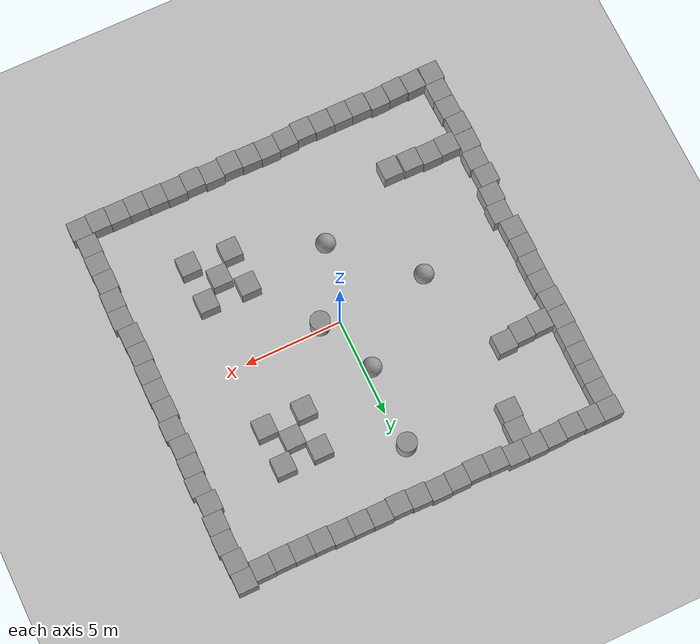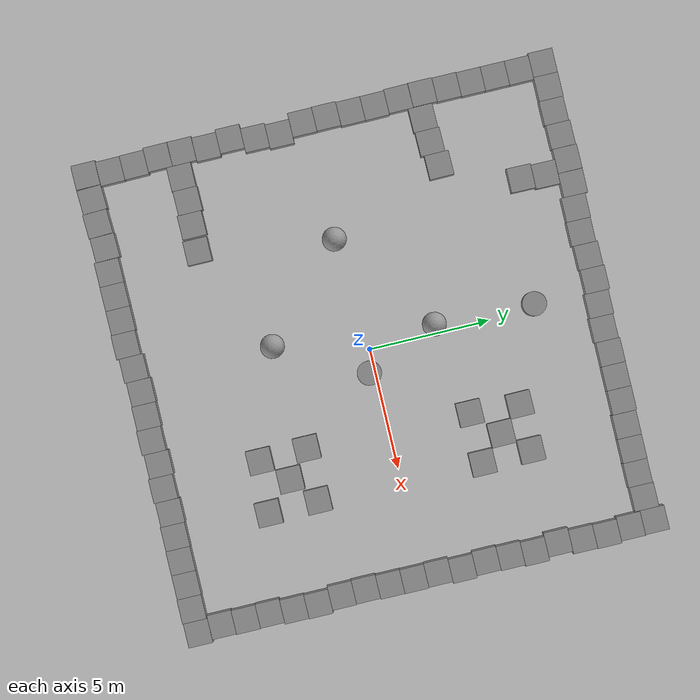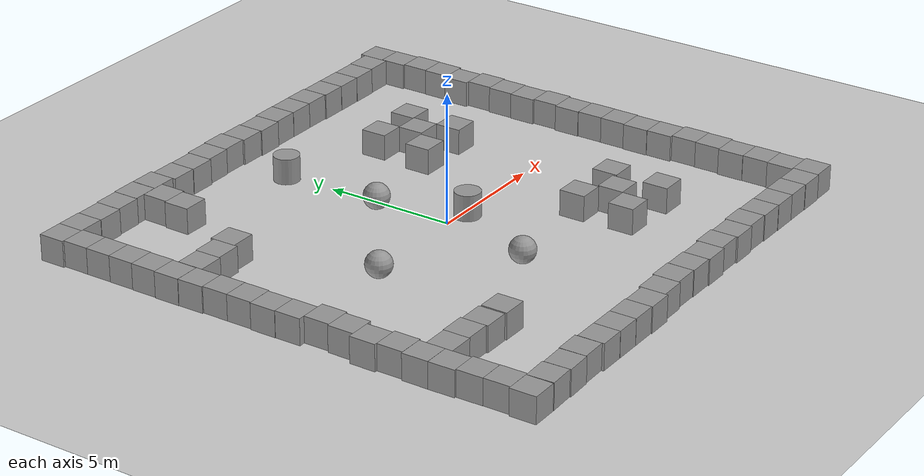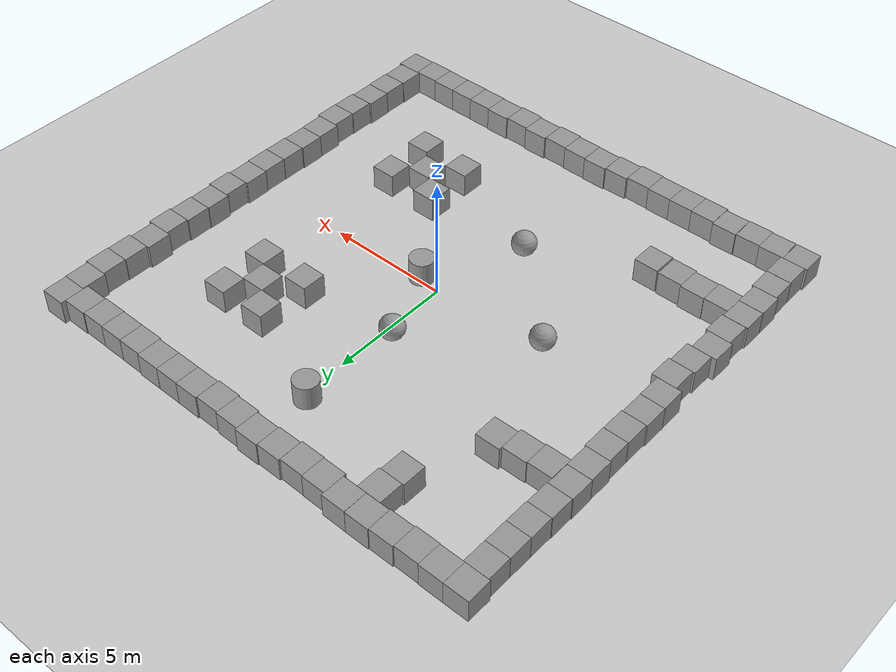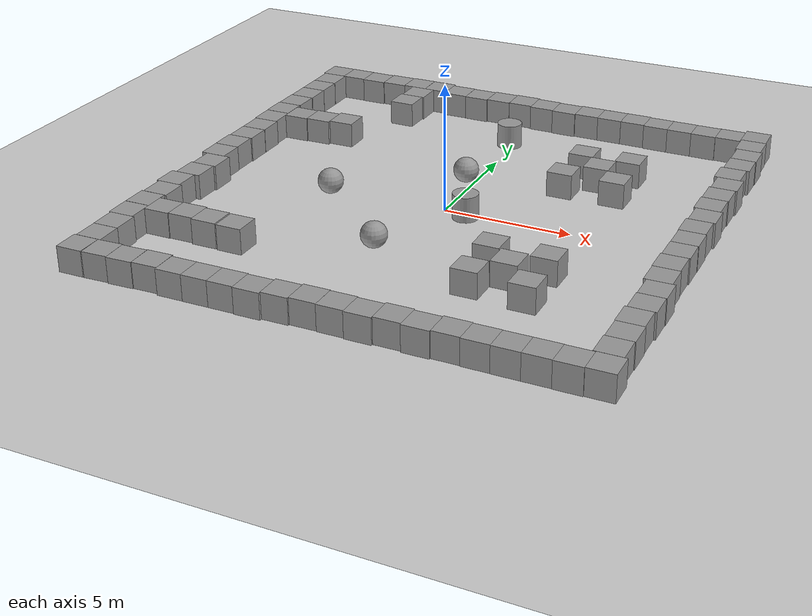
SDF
<sdf version="1.7">
 <world name="default">
  <light name="sun" type="directional">
   <pose>0 0 10 0 -0 0</pose>
   <diffuse>0.8 0.8 0.8 1</diffuse>
   <specular>0.2 0.2 0.2 1</specular>
   <attenuation>
    <range>1000</range>
    <constant>0.9</constant>
    <linear>0.01</linear>
    <quadratic>0.001</quadratic>
   </attenuation>
   <direction>-0.5 0.1 -0.9</direction>
   <spot><inner_angle>0</inner_angle><outer_angle>0</outer_angle><falloff>0</falloff></spot>
  </light>
  <model name="ground_plane">
   <static>1</static>
   <link name="link">
    <collision name="collision">
     <geometry><plane><normal>0 0 1</normal><size>100 100</size></plane></geometry>
     <surface>
      <contact><collide_bitmask>65535</collide_bitmask></contact>
      <friction><ode><mu>100</mu><mu2>50</mu2></ode></friction>
     </surface>
    </collision>
    <visual name="visual">
     <cast_shadows>0</cast_shadows>
     <geometry><plane><normal>0 0 1</normal><size>100 100</size></plane></geometry>
     <material>
      <script><uri>file://media/materials/scripts/gazebo.material</uri><name>Gazebo/Grey</name></script>
     </material>
    </visual>
   </link>
  </model>
  <gravity>0 0 -9.8</gravity>
  <magnetic_field>6e-06 2.3e-05 -4.2e-05</magnetic_field>
  <atmosphere type="adiabatic"/>
  <physics type="ode">
   <max_step_size>0.001</max_step_size>
   <real_time_factor>1</real_time_factor>
   <real_time_update_rate>1000</real_time_update_rate>
  </physics>
  <scene><ambient>0.4 0.4 0.4 1</ambient><background>0.7 0.7 0.7 1</background><shadows>1</shadows></scene>
  <audio><device>default</device></audio>
  <spherical_coordinates>
   <surface_model>EARTH_WGS84</surface_model>
   <latitude_deg>0</latitude_deg>
   <longitude_deg>0</longitude_deg>
   <elevation>0</elevation>
   <heading_deg>0</heading_deg>
  </spherical_coordinates>
  <model name="unit_box">
   <pose>-9.50899 1.49304 0.5 0 -0 0.005509</pose>
   <link name="link">
    <inertial>
     <mass>1</mass>
     <inertia>
      <ixx>0.166667</ixx>
      <ixy>0</ixy>
      <ixz>0</ixz>
      <iyy>0.166667</iyy>
      <iyz>0</iyz>
      <izz>0.166667</izz>
     </inertia>
    </inertial>
    <collision name="collision"><geometry><box><size>1 1 1</size></box></geometry></collision>
    <visual name="visual">
     <geometry><box><size>1 1 1</size></box></geometry>
     <material>
      <script><name>Gazebo/Grey</name><uri>file://media/materials/scripts/gazebo.material</uri></script>
     </material>
    </visual>
   </link>
  </model>
  <model name="unit_box_0">
   <pose>-9.50952 2.49358 0.5 0 -0 0.006554</pose>
   <link name="link">
    <inertial>
     <mass>1</mass>
     <inertia>
      <ixx>0.166667</ixx>
      <ixy>0</ixy>
      <ixz>0</ixz>
      <iyy>0.166667</iyy>
      <iyz>0</iyz>
      <izz>0.166667</izz>
     </inertia>
    </inertial>
    <collision name="collision"><geometry><box><size>1 1 1</size></box></geometry></collision>
    <visual name="visual">
     <geometry><box><size>1 1 1</size></box></geometry>
     <material>
      <script><name>Gazebo/Grey</name><uri>file://media/materials/scripts/gazebo.material</uri></script>
     </material>
    </visual>
   </link>
  </model>
  <model name="unit_box_1">
   <pose>-9.56127 3.49327 0.5 0 -0 0.006556</pose>
   <link name="link">
    <inertial>
     <mass>1</mass>
     <inertia>
      <ixx>0.166667</ixx>
      <ixy>0</ixy>
      <ixz>0</ixz>
      <iyy>0.166667</iyy>
      <iyz>0</iyz>
      <izz>0.166667</izz>
     </inertia>
    </inertial>
    <collision name="collision"><geometry><box><size>1 1 1</size></box></geometry></collision>
    <visual name="visual">
     <geometry><box><size>1 1 1</size></box></geometry>
     <material>
      <script><name>Gazebo/Grey</name><uri>file://media/materials/scripts/gazebo.material</uri></script>
     </material>
    </visual>
   </link>
  </model>
  <model name="unit_box_2">
   <pose>-9.58035 4.49539 0.5 0 -0 0.002115</pose>
   <link name="link">
    <inertial>
     <mass>1</mass>
     <inertia>
      <ixx>0.166667</ixx>
      <ixy>0</ixy>
      <ixz>0</ixz>
      <iyy>0.166667</iyy>
      <iyz>0</iyz>
      <izz>0.166667</izz>
     </inertia>
    </inertial>
    <collision name="collision"><geometry><box><size>1 1 1</size></box></geometry></collision>
    <visual name="visual">
     <geometry><box><size>1 1 1</size></box></geometry>
     <material>
      <script><name>Gazebo/Grey</name><uri>file://media/materials/scripts/gazebo.material</uri></script>
     </material>
    </visual>
   </link>
  </model>
  <model name="unit_box_3">
   <pose>-9.55835 5.49548 0.499995 0 -1e-05 0.002039</pose>
   <link name="link">
    <inertial>
     <mass>1</mass>
     <inertia>
      <ixx>0.166667</ixx>
      <ixy>0</ixy>
      <ixz>0</ixz>
      <iyy>0.166667</iyy>
      <iyz>0</iyz>
      <izz>0.166667</izz>
     </inertia>
    </inertial>
    <collision name="collision"><geometry><box><size>1 1 1</size></box></geometry></collision>
    <visual name="visual">
     <geometry><box><size>1 1 1</size></box></geometry>
     <material>
      <script><name>Gazebo/Grey</name><uri>file://media/materials/scripts/gazebo.material</uri></script>
     </material>
    </visual>
   </link>
  </model>
  <model name="unit_box_4">
   <pose>-9.54098 6.49552 0.499995 -0 1e-05 0.002039</pose>
   <link name="link">
    <inertial>
     <mass>1</mass>
     <inertia>
      <ixx>0.166667</ixx>
      <ixy>0</ixy>
      <ixz>0</ixz>
      <iyy>0.166667</iyy>
      <iyz>0</iyz>
      <izz>0.166667</izz>
     </inertia>
    </inertial>
    <collision name="collision"><geometry><box><size>1 1 1</size></box></geometry></collision>
    <visual name="visual">
     <geometry><box><size>1 1 1</size></box></geometry>
     <material>
      <script><name>Gazebo/Grey</name><uri>file://media/materials/scripts/gazebo.material</uri></script>
     </material>
    </visual>
   </link>
  </model>
  <model name="unit_box_5">
   <pose>-9.54005 7.49553 0.499995 0 1e-05 0.00203</pose>
   <link name="link">
    <inertial>
     <mass>1</mass>
     <inertia>
      <ixx>0.166667</ixx>
      <ixy>0</ixy>
      <ixz>0</ixz>
      <iyy>0.166667</iyy>
      <iyz>0</iyz>
      <izz>0.166667</izz>
     </inertia>
    </inertial>
    <collision name="collision"><geometry><box><size>1 1 1</size></box></geometry></collision>
    <visual name="visual">
     <geometry><box><size>1 1 1</size></box></geometry>
     <material>
      <script><name>Gazebo/Grey</name><uri>file://media/materials/scripts/gazebo.material</uri></script>
     </material>
    </visual>
   </link>
  </model>
  <model name="unit_box_6">
   <pose>-9.53865 8.49559 0.5 0 -0 0.001917</pose>
   <link name="link">
    <inertial>
     <mass>1</mass>
     <inertia>
      <ixx>0.166667</ixx>
      <ixy>0</ixy>
      <ixz>0</ixz>
      <iyy>0.166667</iyy>
      <iyz>0</iyz>
      <izz>0.166667</izz>
     </inertia>
    </inertial>
    <collision name="collision"><geometry><box><size>1 1 1</size></box></geometry></collision>
    <visual name="visual">
     <geometry><box><size>1 1 1</size></box></geometry>
     <material>
      <script><name>Gazebo/Grey</name><uri>file://media/materials/scripts/gazebo.material</uri></script>
     </material>
    </visual>
   </link>
  </model>
  <model name="unit_box_7">
   <pose>-9.61453 9.49573 0.499995 -0 -1e-05 0.001346</pose>
   <link name="link">
    <inertial>
     <mass>1</mass>
     <inertia>
      <ixx>0.166667</ixx>
      <ixy>0</ixy>
      <ixz>0</ixz>
      <iyy>0.166667</iyy>
      <iyz>0</iyz>
      <izz>0.166667</izz>
     </inertia>
    </inertial>
    <collision name="collision"><geometry><box><size>1 1 1</size></box></geometry></collision>
    <visual name="visual">
     <geometry><box><size>1 1 1</size></box></geometry>
     <material>
      <script><name>Gazebo/Grey</name><uri>file://media/materials/scripts/gazebo.material</uri></script>
     </material>
    </visual>
   </link>
  </model>
  <model name="unit_box_8">
   <pose>-8.61421 9.49686 0.499995 -1e-05 -0 0.00071</pose>
   <link name="link">
    <inertial>
     <mass>1</mass>
     <inertia>
      <ixx>0.166667</ixx>
      <ixy>0</ixy>
      <ixz>0</ixz>
      <iyy>0.166667</iyy>
      <iyz>0</iyz>
      <izz>0.166667</izz>
     </inertia>
    </inertial>
    <collision name="collision"><geometry><box><size>1 1 1</size></box></geometry></collision>
    <visual name="visual">
     <geometry><box><size>1 1 1</size></box></geometry>
     <material>
      <script><name>Gazebo/Grey</name><uri>file://media/materials/scripts/gazebo.material</uri></script>
     </material>
    </visual>
   </link>
  </model>
  <model name="unit_box_9">
   <pose>-7.61401 9.4805 0.5 0 -0 0.001055</pose>
   <link name="link">
    <inertial>
     <mass>1</mass>
     <inertia>
      <ixx>0.166667</ixx>
      <ixy>0</ixy>
      <ixz>0</ixz>
      <iyy>0.166667</iyy>
      <iyz>0</iyz>
      <izz>0.166667</izz>
     </inertia>
    </inertial>
    <collision name="collision"><geometry><box><size>1 1 1</size></box></geometry></collision>
    <visual name="visual">
     <geometry><box><size>1 1 1</size></box></geometry>
     <material>
      <script><name>Gazebo/Grey</name><uri>file://media/materials/scripts/gazebo.material</uri></script>
     </material>
    </visual>
   </link>
  </model>
  <model name="unit_box_10">
   <pose>-6.61379 9.52635 0.499995 -1e-05 -0 0.001648</pose>
   <link name="link">
    <inertial>
     <mass>1</mass>
     <inertia>
      <ixx>0.166667</ixx>
      <ixy>0</ixy>
      <ixz>0</ixz>
      <iyy>0.166667</iyy>
      <iyz>0</iyz>
      <izz>0.166667</izz>
     </inertia>
    </inertial>
    <collision name="collision"><geometry><box><size>1 1 1</size></box></geometry></collision>
    <visual name="visual">
     <geometry><box><size>1 1 1</size></box></geometry>
     <material>
      <script><name>Gazebo/Grey</name><uri>file://media/materials/scripts/gazebo.material</uri></script>
     </material>
    </visual>
   </link>
  </model>
  <model name="unit_box_11">
   <pose>-5.6125 9.56164 0.499995 0 -1e-05 0.001868</pose>
   <link name="link">
    <inertial>
     <mass>1</mass>
     <inertia>
      <ixx>0.166667</ixx>
      <ixy>0</ixy>
      <ixz>0</ixz>
      <iyy>0.166667</iyy>
      <iyz>0</iyz>
      <izz>0.166667</izz>
     </inertia>
    </inertial>
    <collision name="collision"><geometry><box><size>1 1 1</size></box></geometry></collision>
    <visual name="visual">
     <geometry><box><size>1 1 1</size></box></geometry>
     <material>
      <script><name>Gazebo/Grey</name><uri>file://media/materials/scripts/gazebo.material</uri></script>
     </material>
    </visual>
   </link>
  </model>
  <model name="unit_box_12">
   <pose>-4.60885 9.55498 0.499995 -0 1e-05 -0.005478</pose>
   <link name="link">
    <inertial>
     <mass>1</mass>
     <inertia>
      <ixx>0.166667</ixx>
      <ixy>0</ixy>
      <ixz>0</ixz>
      <iyy>0.166667</iyy>
      <iyz>0</iyz>
      <izz>0.166667</izz>
     </inertia>
    </inertial>
    <collision name="collision"><geometry><box><size>1 1 1</size></box></geometry></collision>
    <visual name="visual">
     <geometry><box><size>1 1 1</size></box></geometry>
     <material>
      <script><name>Gazebo/Grey</name><uri>file://media/materials/scripts/gazebo.material</uri></script>
     </material>
    </visual>
   </link>
  </model>
  <model name="unit_box_13">
   <pose>-3.60929 9.43516 0.499995 -0 1e-05 -0.005322</pose>
   <link name="link">
    <inertial>
     <mass>1</mass>
     <inertia>
      <ixx>0.166667</ixx>
      <ixy>0</ixy>
      <ixz>0</ixz>
      <iyy>0.166667</iyy>
      <iyz>0</iyz>
      <izz>0.166667</izz>
     </inertia>
    </inertial>
    <collision name="collision"><geometry><box><size>1 1 1</size></box></geometry></collision>
    <visual name="visual">
     <geometry><box><size>1 1 1</size></box></geometry>
     <material>
      <script><name>Gazebo/Grey</name><uri>file://media/materials/scripts/gazebo.material</uri></script>
     </material>
    </visual>
   </link>
  </model>
  <model name="unit_box_14">
   <pose>-2.60927 9.41078 0.499995 -1e-05 -0 -0.005189</pose>
   <link name="link">
    <inertial>
     <mass>1</mass>
     <inertia>
      <ixx>0.166667</ixx>
      <ixy>0</ixy>
      <ixz>0</ixz>
      <iyy>0.166667</iyy>
      <iyz>0</iyz>
      <izz>0.166667</izz>
     </inertia>
    </inertial>
    <collision name="collision"><geometry><box><size>1 1 1</size></box></geometry></collision>
    <visual name="visual">
     <geometry><box><size>1 1 1</size></box></geometry>
     <material>
      <script><name>Gazebo/Grey</name><uri>file://media/materials/scripts/gazebo.material</uri></script>
     </material>
    </visual>
   </link>
  </model>
  <model name="unit_box_15">
   <pose>-1.60787 9.47219 0.499995 1e-05 -0 -0.002718</pose>
   <link name="link">
    <inertial>
     <mass>1</mass>
     <inertia>
      <ixx>0.166667</ixx>
      <ixy>0</ixy>
      <ixz>0</ixz>
      <iyy>0.166667</iyy>
      <iyz>0</iyz>
      <izz>0.166667</izz>
     </inertia>
    </inertial>
    <collision name="collision"><geometry><box><size>1 1 1</size></box></geometry></collision>
    <visual name="visual">
     <geometry><box><size>1 1 1</size></box></geometry>
     <material>
      <script><name>Gazebo/Grey</name><uri>file://media/materials/scripts/gazebo.material</uri></script>
     </material>
    </visual>
   </link>
  </model>
  <model name="unit_box_16">
   <pose>-0.607715 9.5092 0.499995 1e-05 -0 -0.002661</pose>
   <link name="link">
    <inertial>
     <mass>1</mass>
     <inertia>
      <ixx>0.166667</ixx>
      <ixy>0</ixy>
      <ixz>0</ixz>
      <iyy>0.166667</iyy>
      <iyz>0</iyz>
      <izz>0.166667</izz>
     </inertia>
    </inertial>
    <collision name="collision"><geometry><box><size>1 1 1</size></box></geometry></collision>
    <visual name="visual">
     <geometry><box><size>1 1 1</size></box></geometry>
     <material>
      <script><name>Gazebo/Grey</name><uri>file://media/materials/scripts/gazebo.material</uri></script>
     </material>
    </visual>
   </link>
  </model>
  <model name="unit_box_17">
   <pose>0.392104 9.43689 0.499995 -1e-05 -0 -0.002647</pose>
   <link name="link">
    <inertial>
     <mass>1</mass>
     <inertia>
      <ixx>0.166667</ixx>
      <ixy>0</ixy>
      <ixz>0</ixz>
      <iyy>0.166667</iyy>
      <iyz>0</iyz>
      <izz>0.166667</izz>
     </inertia>
    </inertial>
    <collision name="collision"><geometry><box><size>1 1 1</size></box></geometry></collision>
    <visual name="visual">
     <geometry><box><size>1 1 1</size></box></geometry>
     <material>
      <script><name>Gazebo/Grey</name><uri>file://media/materials/scripts/gazebo.material</uri></script>
     </material>
    </visual>
   </link>
  </model>
  <model name="unit_box_18">
   <pose>1.39199 9.39251 0.499995 1e-05 -0 -0.00264</pose>
   <link name="link">
    <inertial>
     <mass>1</mass>
     <inertia>
      <ixx>0.166667</ixx>
      <ixy>0</ixy>
      <ixz>0</ixz>
      <iyy>0.166667</iyy>
      <iyz>0</iyz>
      <izz>0.166667</izz>
     </inertia>
    </inertial>
    <collision name="collision"><geometry><box><size>1 1 1</size></box></geometry></collision>
    <visual name="visual">
     <geometry><box><size>1 1 1</size></box></geometry>
     <material>
      <script><name>Gazebo/Grey</name><uri>file://media/materials/scripts/gazebo.material</uri></script>
     </material>
    </visual>
   </link>
  </model>
  <model name="unit_box_19">
   <pose>2.39259 9.43873 0.499995 -1e-05 -0 -0.001596</pose>
   <link name="link">
    <inertial>
     <mass>1</mass>
     <inertia>
      <ixx>0.166667</ixx>
      <ixy>0</ixy>
      <ixz>0</ixz>
      <iyy>0.166667</iyy>
      <iyz>0</iyz>
      <izz>0.166667</izz>
     </inertia>
    </inertial>
    <collision name="collision"><geometry><box><size>1 1 1</size></box></geometry></collision>
    <visual name="visual">
     <geometry><box><size>1 1 1</size></box></geometry>
     <material>
      <script><name>Gazebo/Grey</name><uri>file://media/materials/scripts/gazebo.material</uri></script>
     </material>
    </visual>
   </link>
  </model>
  <model name="unit_box_20">
   <pose>3.3927 9.42968 0.499995 -1e-05 -0 -0.001365</pose>
   <link name="link">
    <inertial>
     <mass>1</mass>
     <inertia>
      <ixx>0.166667</ixx>
      <ixy>0</ixy>
      <ixz>0</ixz>
      <iyy>0.166667</iyy>
      <iyz>0</iyz>
      <izz>0.166667</izz>
     </inertia>
    </inertial>
    <collision name="collision"><geometry><box><size>1 1 1</size></box></geometry></collision>
    <visual name="visual">
     <geometry><box><size>1 1 1</size></box></geometry>
     <material>
      <script><name>Gazebo/Grey</name><uri>file://media/materials/scripts/gazebo.material</uri></script>
     </material>
    </visual>
   </link>
  </model>
  <model name="unit_box_21">
   <pose>4.39287 9.43126 0.499995 1e-05 -0 -0.001029</pose>
   <link name="link">
    <inertial>
     <mass>1</mass>
     <inertia>
      <ixx>0.166667</ixx>
      <ixy>0</ixy>
      <ixz>0</ixz>
      <iyy>0.166667</iyy>
      <iyz>0</iyz>
      <izz>0.166667</izz>
     </inertia>
    </inertial>
    <collision name="collision"><geometry><box><size>1 1 1</size></box></geometry></collision>
    <visual name="visual">
     <geometry><box><size>1 1 1</size></box></geometry>
     <material>
      <script><name>Gazebo/Grey</name><uri>file://media/materials/scripts/gazebo.material</uri></script>
     </material>
    </visual>
   </link>
  </model>
  <model name="unit_box_22">
   <pose>5.3933 9.3867 0.5 0 0 -7.4e-05</pose>
   <link name="link">
    <inertial>
     <mass>1</mass>
     <inertia>
      <ixx>0.166667</ixx>
      <ixy>0</ixy>
      <ixz>0</ixz>
      <iyy>0.166667</iyy>
      <iyz>0</iyz>
      <izz>0.166667</izz>
     </inertia>
    </inertial>
    <collision name="collision"><geometry><box><size>1 1 1</size></box></geometry></collision>
    <visual name="visual">
     <geometry><box><size>1 1 1</size></box></geometry>
     <material>
      <script><name>Gazebo/Grey</name><uri>file://media/materials/scripts/gazebo.material</uri></script>
     </material>
    </visual>
   </link>
  </model>
  <model name="unit_box_23">
   <pose>6.39336 9.37988 0.499995 1e-05 -0 3.2e-05</pose>
   <link name="link">
    <inertial>
     <mass>1</mass>
     <inertia>
      <ixx>0.166667</ixx>
      <ixy>0</ixy>
      <ixz>0</ixz>
      <iyy>0.166667</iyy>
      <iyz>0</iyz>
      <izz>0.166667</izz>
     </inertia>
    </inertial>
    <collision name="collision"><geometry><box><size>1 1 1</size></box></geometry></collision>
    <visual name="visual">
     <geometry><box><size>1 1 1</size></box></geometry>
     <material>
      <script><name>Gazebo/Grey</name><uri>file://media/materials/scripts/gazebo.material</uri></script>
     </material>
    </visual>
   </link>
  </model>
  <model name="unit_box_24">
   <pose>7.39336 9.36883 0.499995 0 -9e-06 3.5e-05</pose>
   <link name="link">
    <inertial>
     <mass>1</mass>
     <inertia>
      <ixx>0.166667</ixx>
      <ixy>0</ixy>
      <ixz>0</ixz>
      <iyy>0.166667</iyy>
      <iyz>0</iyz>
      <izz>0.166667</izz>
     </inertia>
    </inertial>
    <collision name="collision"><geometry><box><size>1 1 1</size></box></geometry></collision>
    <visual name="visual">
     <geometry><box><size>1 1 1</size></box></geometry>
     <material>
      <script><name>Gazebo/Grey</name><uri>file://media/materials/scripts/gazebo.material</uri></script>
     </material>
    </visual>
   </link>
  </model>
  <model name="unit_box_25">
   <pose>8.39341 9.39466 0.5 0 -0 0.000138</pose>
   <link name="link">
    <inertial>
     <mass>1</mass>
     <inertia>
      <ixx>0.166667</ixx>
      <ixy>0</ixy>
      <ixz>0</ixz>
      <iyy>0.166667</iyy>
      <iyz>0</iyz>
      <izz>0.166667</izz>
     </inertia>
    </inertial>
    <collision name="collision"><geometry><box><size>1 1 1</size></box></geometry></collision>
    <visual name="visual">
     <geometry><box><size>1 1 1</size></box></geometry>
     <material>
      <script><name>Gazebo/Grey</name><uri>file://media/materials/scripts/gazebo.material</uri></script>
     </material>
    </visual>
   </link>
  </model>
  <model name="unit_box_26">
   <pose>9.39342 9.59434 0.5 0 -0 0.000231</pose>
   <link name="link">
    <inertial>
     <mass>1</mass>
     <inertia>
      <ixx>0.166667</ixx>
      <ixy>0</ixy>
      <ixz>0</ixz>
      <iyy>0.166667</iyy>
      <iyz>0</iyz>
      <izz>0.166667</izz>
     </inertia>
    </inertial>
    <collision name="collision"><geometry><box><size>1 1 1</size></box></geometry></collision>
    <visual name="visual">
     <geometry><box><size>1 1 1</size></box></geometry>
     <material>
      <script><name>Gazebo/Grey</name><uri>file://media/materials/scripts/gazebo.material</uri></script>
     </material>
    </visual>
   </link>
  </model>
  <model name="unit_box_27">
   <pose>9.41864 8.59421 0.499995 0 -1e-05 0.000412</pose>
   <link name="link">
    <inertial>
     <mass>1</mass>
     <inertia>
      <ixx>0.166667</ixx>
      <ixy>0</ixy>
      <ixz>0</ixz>
      <iyy>0.166667</iyy>
      <iyz>0</iyz>
      <izz>0.166667</izz>
     </inertia>
    </inertial>
    <collision name="collision"><geometry><box><size>1 1 1</size></box></geometry></collision>
    <visual name="visual">
     <geometry><box><size>1 1 1</size></box></geometry>
     <material>
      <script><name>Gazebo/Grey</name><uri>file://media/materials/scripts/gazebo.material</uri></script>
     </material>
    </visual>
   </link>
  </model>
  <model name="unit_box_28">
   <pose>9.4967 7.59422 0.499995 0 -1e-05 0.000448</pose>
   <link name="link">
    <inertial>
     <mass>1</mass>
     <inertia>
      <ixx>0.166667</ixx>
      <ixy>0</ixy>
      <ixz>0</ixz>
      <iyy>0.166667</iyy>
      <iyz>0</iyz>
      <izz>0.166667</izz>
     </inertia>
    </inertial>
    <collision name="collision"><geometry><box><size>1 1 1</size></box></geometry></collision>
    <visual name="visual">
     <geometry><box><size>1 1 1</size></box></geometry>
     <material>
      <script><name>Gazebo/Grey</name><uri>file://media/materials/scripts/gazebo.material</uri></script>
     </material>
    </visual>
   </link>
  </model>
  <model name="unit_box_29">
   <pose>9.47494 6.5942 0.499995 0 1e-05 0.000465</pose>
   <link name="link">
    <inertial>
     <mass>1</mass>
     <inertia>
      <ixx>0.166667</ixx>
      <ixy>0</ixy>
      <ixz>0</ixz>
      <iyy>0.166667</iyy>
      <iyz>0</iyz>
      <izz>0.166667</izz>
     </inertia>
    </inertial>
    <collision name="collision"><geometry><box><size>1 1 1</size></box></geometry></collision>
    <visual name="visual">
     <geometry><box><size>1 1 1</size></box></geometry>
     <material>
      <script><name>Gazebo/Grey</name><uri>file://media/materials/scripts/gazebo.material</uri></script>
     </material>
    </visual>
   </link>
  </model>
  <model name="unit_box_30">
   <pose>9.3665 5.5939 0.499995 0 1e-05 0.000959</pose>
   <link name="link">
    <inertial>
     <mass>1</mass>
     <inertia>
      <ixx>0.166667</ixx>
      <ixy>0</ixy>
      <ixz>0</ixz>
      <iyy>0.166667</iyy>
      <iyz>0</iyz>
      <izz>0.166667</izz>
     </inertia>
    </inertial>
    <collision name="collision"><geometry><box><size>1 1 1</size></box></geometry></collision>
    <visual name="visual">
     <geometry><box><size>1 1 1</size></box></geometry>
     <material>
      <script><name>Gazebo/Grey</name><uri>file://media/materials/scripts/gazebo.material</uri></script>
     </material>
    </visual>
   </link>
  </model>
  <model name="unit_box_31">
   <pose>9.50773 4.59387 0.5 0 -0 0.001405</pose>
   <link name="link">
    <inertial>
     <mass>1</mass>
     <inertia>
      <ixx>0.166667</ixx>
      <ixy>0</ixy>
      <ixz>0</ixz>
      <iyy>0.166667</iyy>
      <iyz>0</iyz>
      <izz>0.166667</izz>
     </inertia>
    </inertial>
    <collision name="collision"><geometry><box><size>1 1 1</size></box></geometry></collision>
    <visual name="visual">
     <geometry><box><size>1 1 1</size></box></geometry>
     <material>
      <script><name>Gazebo/Grey</name><uri>file://media/materials/scripts/gazebo.material</uri></script>
     </material>
    </visual>
   </link>
  </model>
  <model name="unit_box_32">
   <pose>9.44971 3.59376 0.5 0 -0 0.001459</pose>
   <link name="link">
    <inertial>
     <mass>1</mass>
     <inertia>
      <ixx>0.166667</ixx>
      <ixy>0</ixy>
      <ixz>0</ixz>
      <iyy>0.166667</iyy>
      <iyz>0</iyz>
      <izz>0.166667</izz>
     </inertia>
    </inertial>
    <collision name="collision"><geometry><box><size>1 1 1</size></box></geometry></collision>
    <visual name="visual">
     <geometry><box><size>1 1 1</size></box></geometry>
     <material>
      <script><name>Gazebo/Grey</name><uri>file://media/materials/scripts/gazebo.material</uri></script>
     </material>
    </visual>
   </link>
  </model>
  <model name="unit_box_33">
   <pose>9.41921 2.59371 0.5 0 -0 0.001467</pose>
   <link name="link">
    <inertial>
     <mass>1</mass>
     <inertia>
      <ixx>0.166667</ixx>
      <ixy>0</ixy>
      <ixz>0</ixz>
      <iyy>0.166667</iyy>
      <iyz>0</iyz>
      <izz>0.166667</izz>
     </inertia>
    </inertial>
    <collision name="collision"><geometry><box><size>1 1 1</size></box></geometry></collision>
    <visual name="visual">
     <geometry><box><size>1 1 1</size></box></geometry>
     <material>
      <script><name>Gazebo/Grey</name><uri>file://media/materials/scripts/gazebo.material</uri></script>
     </material>
    </visual>
   </link>
  </model>
  <model name="unit_box_34">
   <pose>9.5007 1.59379 0.499995 0 1e-05 0.001543</pose>
   <link name="link">
    <inertial>
     <mass>1</mass>
     <inertia>
      <ixx>0.166667</ixx>
      <ixy>0</ixy>
      <ixz>0</ixz>
      <iyy>0.166667</iyy>
      <iyz>0</iyz>
      <izz>0.166667</izz>
     </inertia>
    </inertial>
    <collision name="collision"><geometry><box><size>1 1 1</size></box></geometry></collision>
    <visual name="visual">
     <geometry><box><size>1 1 1</size></box></geometry>
     <material>
      <script><name>Gazebo/Grey</name><uri>file://media/materials/scripts/gazebo.material</uri></script>
     </material>
    </visual>
   </link>
  </model>
  <model name="unit_box_35">
   <pose>9.42391 0.593644 0.499995 -1e-05 0 0.001598</pose>
   <link name="link">
    <inertial>
     <mass>1</mass>
     <inertia>
      <ixx>0.166667</ixx>
      <ixy>0</ixy>
      <ixz>0</ixz>
      <iyy>0.166667</iyy>
      <iyz>0</iyz>
      <izz>0.166667</izz>
     </inertia>
    </inertial>
    <collision name="collision"><geometry><box><size>1 1 1</size></box></geometry></collision>
    <visual name="visual">
     <geometry><box><size>1 1 1</size></box></geometry>
     <material>
      <script><name>Gazebo/Grey</name><uri>file://media/materials/scripts/gazebo.material</uri></script>
     </material>
    </visual>
   </link>
  </model>
  <model name="unit_box_36">
   <pose>9.45116 -0.406327 0.5 0 -0 0.001604</pose>
   <link name="link">
    <inertial>
     <mass>1</mass>
     <inertia>
      <ixx>0.166667</ixx>
      <ixy>0</ixy>
      <ixz>0</ixz>
      <iyy>0.166667</iyy>
      <iyz>0</iyz>
      <izz>0.166667</izz>
     </inertia>
    </inertial>
    <collision name="collision"><geometry><box><size>1 1 1</size></box></geometry></collision>
    <visual name="visual">
     <geometry><box><size>1 1 1</size></box></geometry>
     <material>
      <script><name>Gazebo/Grey</name><uri>file://media/materials/scripts/gazebo.material</uri></script>
     </material>
    </visual>
   </link>
  </model>
  <model name="unit_box_37">
   <pose>9.43995 -1.40635 0.499995 0 1e-05 0.00161</pose>
   <link name="link">
    <inertial>
     <mass>1</mass>
     <inertia>
      <ixx>0.166667</ixx>
      <ixy>0</ixy>
      <ixz>0</ixz>
      <iyy>0.166667</iyy>
      <iyz>0</iyz>
      <izz>0.166667</izz>
     </inertia>
    </inertial>
    <collision name="collision"><geometry><box><size>1 1 1</size></box></geometry></collision>
    <visual name="visual">
     <geometry><box><size>1 1 1</size></box></geometry>
     <material>
      <script><name>Gazebo/Grey</name><uri>file://media/materials/scripts/gazebo.material</uri></script>
     </material>
    </visual>
   </link>
  </model>
  <model name="unit_box_38">
   <pose>9.40094 -2.40643 0.499995 0 -1e-05 0.001587</pose>
   <link name="link">
    <inertial>
     <mass>1</mass>
     <inertia>
      <ixx>0.166667</ixx>
      <ixy>0</ixy>
      <ixz>0</ixz>
      <iyy>0.166667</iyy>
      <iyz>0</iyz>
      <izz>0.166667</izz>
     </inertia>
    </inertial>
    <collision name="collision"><geometry><box><size>1 1 1</size></box></geometry></collision>
    <visual name="visual">
     <geometry><box><size>1 1 1</size></box></geometry>
     <material>
      <script><name>Gazebo/Grey</name><uri>file://media/materials/scripts/gazebo.material</uri></script>
     </material>
    </visual>
   </link>
  </model>
  <model name="unit_box_39">
   <pose>9.42291 -3.40641 0.499995 0 -1e-05 0.001577</pose>
   <link name="link">
    <inertial>
     <mass>1</mass>
     <inertia>
      <ixx>0.166667</ixx>
      <ixy>0</ixy>
      <ixz>0</ixz>
      <iyy>0.166667</iyy>
      <iyz>0</iyz>
      <izz>0.166667</izz>
     </inertia>
    </inertial>
    <collision name="collision"><geometry><box><size>1 1 1</size></box></geometry></collision>
    <visual name="visual">
     <geometry><box><size>1 1 1</size></box></geometry>
     <material>
      <script><name>Gazebo/Grey</name><uri>file://media/materials/scripts/gazebo.material</uri></script>
     </material>
    </visual>
   </link>
  </model>
  <model name="unit_box_40">
   <pose>9.53445 -4.40625 0.499995 -0 1e-05 0.001555</pose>
   <link name="link">
    <inertial>
     <mass>1</mass>
     <inertia>
      <ixx>0.166667</ixx>
      <ixy>0</ixy>
      <ixz>0</ixz>
      <iyy>0.166667</iyy>
      <iyz>0</iyz>
      <izz>0.166667</izz>
     </inertia>
    </inertial>
    <collision name="collision"><geometry><box><size>1 1 1</size></box></geometry></collision>
    <visual name="visual">
     <geometry><box><size>1 1 1</size></box></geometry>
     <material>
      <script><name>Gazebo/Grey</name><uri>file://media/materials/scripts/gazebo.material</uri></script>
     </material>
    </visual>
   </link>
  </model>
  <model name="unit_box_41">
   <pose>9.51364 -5.40629 0.499995 0 1e-05 0.001554</pose>
   <link name="link">
    <inertial>
     <mass>1</mass>
     <inertia>
      <ixx>0.166667</ixx>
      <ixy>0</ixy>
      <ixz>0</ixz>
      <iyy>0.166667</iyy>
      <iyz>0</iyz>
      <izz>0.166667</izz>
     </inertia>
    </inertial>
    <collision name="collision"><geometry><box><size>1 1 1</size></box></geometry></collision>
    <visual name="visual">
     <geometry><box><size>1 1 1</size></box></geometry>
     <material>
      <script><name>Gazebo/Grey</name><uri>file://media/materials/scripts/gazebo.material</uri></script>
     </material>
    </visual>
   </link>
  </model>
  <model name="unit_box_42">
   <pose>9.44409 -6.40641 0.499995 -1e-05 -0 0.001525</pose>
   <link name="link">
    <inertial>
     <mass>1</mass>
     <inertia>
      <ixx>0.166667</ixx>
      <ixy>0</ixy>
      <ixz>0</ixz>
      <iyy>0.166667</iyy>
      <iyz>0</iyz>
      <izz>0.166667</izz>
     </inertia>
    </inertial>
    <collision name="collision"><geometry><box><size>1 1 1</size></box></geometry></collision>
    <visual name="visual">
     <geometry><box><size>1 1 1</size></box></geometry>
     <material>
      <script><name>Gazebo/Grey</name><uri>file://media/materials/scripts/gazebo.material</uri></script>
     </material>
    </visual>
   </link>
  </model>
  <model name="unit_box_43">
   <pose>9.46387 -7.4064 0.499995 1e-05 -0 0.001525</pose>
   <link name="link">
    <inertial>
     <mass>1</mass>
     <inertia>
      <ixx>0.166667</ixx>
      <ixy>0</ixy>
      <ixz>0</ixz>
      <iyy>0.166667</iyy>
      <iyz>0</iyz>
      <izz>0.166667</izz>
     </inertia>
    </inertial>
    <collision name="collision"><geometry><box><size>1 1 1</size></box></geometry></collision>
    <visual name="visual">
     <geometry><box><size>1 1 1</size></box></geometry>
     <material>
      <script><name>Gazebo/Grey</name><uri>file://media/materials/scripts/gazebo.material</uri></script>
     </material>
    </visual>
   </link>
  </model>
  <model name="unit_box_44">
   <pose>9.43884 -8.40645 0.499995 -1e-05 -0 0.00148</pose>
   <link name="link">
    <inertial>
     <mass>1</mass>
     <inertia>
      <ixx>0.166667</ixx>
      <ixy>0</ixy>
      <ixz>0</ixz>
      <iyy>0.166667</iyy>
      <iyz>0</iyz>
      <izz>0.166667</izz>
     </inertia>
    </inertial>
    <collision name="collision"><geometry><box><size>1 1 1</size></box></geometry></collision>
    <visual name="visual">
     <geometry><box><size>1 1 1</size></box></geometry>
     <material>
      <script><name>Gazebo/Grey</name><uri>file://media/materials/scripts/gazebo.material</uri></script>
     </material>
    </visual>
   </link>
  </model>
  <model name="unit_box_45">
   <pose>9.54897 -9.40793 0.499995 1e-05 -0 -0.000979</pose>
   <link name="link">
    <inertial>
     <mass>1</mass>
     <inertia>
      <ixx>0.166667</ixx>
      <ixy>0</ixy>
      <ixz>0</ixz>
      <iyy>0.166667</iyy>
      <iyz>0</iyz>
      <izz>0.166667</izz>
     </inertia>
    </inertial>
    <collision name="collision"><geometry><box><size>1 1 1</size></box></geometry></collision>
    <visual name="visual">
     <geometry><box><size>1 1 1</size></box></geometry>
     <material>
      <script><name>Gazebo/Grey</name><uri>file://media/materials/scripts/gazebo.material</uri></script>
     </material>
    </visual>
   </link>
  </model>
  <model name="unit_box_46">
   <pose>8.54892 -9.43225 0.499995 1e-05 0 -0.000931</pose>
   <link name="link">
    <inertial>
     <mass>1</mass>
     <inertia>
      <ixx>0.166667</ixx>
      <ixy>0</ixy>
      <ixz>0</ixz>
      <iyy>0.166667</iyy>
      <iyz>0</iyz>
      <izz>0.166667</izz>
     </inertia>
    </inertial>
    <collision name="collision"><geometry><box><size>1 1 1</size></box></geometry></collision>
    <visual name="visual">
     <geometry><box><size>1 1 1</size></box></geometry>
     <material>
      <script><name>Gazebo/Grey</name><uri>file://media/materials/scripts/gazebo.material</uri></script>
     </material>
    </visual>
   </link>
  </model>
  <model name="unit_box_47">
   <pose>7.54892 -9.41411 0.499995 -1e-05 -0 -0.000917</pose>
   <link name="link">
    <inertial>
     <mass>1</mass>
     <inertia>
      <ixx>0.166667</ixx>
      <ixy>0</ixy>
      <ixz>0</ixz>
      <iyy>0.166667</iyy>
      <iyz>0</iyz>
      <izz>0.166667</izz>
     </inertia>
    </inertial>
    <collision name="collision"><geometry><box><size>1 1 1</size></box></geometry></collision>
    <visual name="visual">
     <geometry><box><size>1 1 1</size></box></geometry>
     <material>
      <script><name>Gazebo/Grey</name><uri>file://media/materials/scripts/gazebo.material</uri></script>
     </material>
    </visual>
   </link>
  </model>
  <model name="unit_box_48">
   <pose>6.5489 -9.41348 0.499995 1e-05 0 -0.00088</pose>
   <link name="link">
    <inertial>
     <mass>1</mass>
     <inertia>
      <ixx>0.166667</ixx>
      <ixy>0</ixy>
      <ixz>0</ixz>
      <iyy>0.166667</iyy>
      <iyz>0</iyz>
      <izz>0.166667</izz>
     </inertia>
    </inertial>
    <collision name="collision"><geometry><box><size>1 1 1</size></box></geometry></collision>
    <visual name="visual">
     <geometry><box><size>1 1 1</size></box></geometry>
     <material>
      <script><name>Gazebo/Grey</name><uri>file://media/materials/scripts/gazebo.material</uri></script>
     </material>
    </visual>
   </link>
  </model>
  <model name="unit_box_49">
   <pose>5.54888 -9.4 0.5 0 -0 -0.000815</pose>
   <link name="link">
    <inertial>
     <mass>1</mass>
     <inertia>
      <ixx>0.166667</ixx>
      <ixy>0</ixy>
      <ixz>0</ixz>
      <iyy>0.166667</iyy>
      <iyz>0</iyz>
      <izz>0.166667</izz>
     </inertia>
    </inertial>
    <collision name="collision"><geometry><box><size>1 1 1</size></box></geometry></collision>
    <visual name="visual">
     <geometry><box><size>1 1 1</size></box></geometry>
     <material>
      <script><name>Gazebo/Grey</name><uri>file://media/materials/scripts/gazebo.material</uri></script>
     </material>
    </visual>
   </link>
  </model>
  <model name="unit_box_50">
   <pose>4.5489 -9.36806 0.499995 0 1e-05 -0.000805</pose>
   <link name="link">
    <inertial>
     <mass>1</mass>
     <inertia>
      <ixx>0.166667</ixx>
      <ixy>0</ixy>
      <ixz>0</ixz>
      <iyy>0.166667</iyy>
      <iyz>0</iyz>
      <izz>0.166667</izz>
     </inertia>
    </inertial>
    <collision name="collision"><geometry><box><size>1 1 1</size></box></geometry></collision>
    <visual name="visual">
     <geometry><box><size>1 1 1</size></box></geometry>
     <material>
      <script><name>Gazebo/Grey</name><uri>file://media/materials/scripts/gazebo.material</uri></script>
     </material>
    </visual>
   </link>
  </model>
  <model name="unit_box_51">
   <pose>3.54802 -9.42109 0.5 0 -0 0.001047</pose>
   <link name="link">
    <inertial>
     <mass>1</mass>
     <inertia>
      <ixx>0.166667</ixx>
      <ixy>0</ixy>
      <ixz>0</ixz>
      <iyy>0.166667</iyy>
      <iyz>0</iyz>
      <izz>0.166667</izz>
     </inertia>
    </inertial>
    <collision name="collision"><geometry><box><size>1 1 1</size></box></geometry></collision>
    <visual name="visual">
     <geometry><box><size>1 1 1</size></box></geometry>
     <material>
      <script><name>Gazebo/Grey</name><uri>file://media/materials/scripts/gazebo.material</uri></script>
     </material>
    </visual>
   </link>
  </model>
  <model name="unit_box_52">
   <pose>2.54792 -9.36159 0.499995 0 9e-06 0.001139</pose>
   <link name="link">
    <inertial>
     <mass>1</mass>
     <inertia>
      <ixx>0.166667</ixx>
      <ixy>0</ixy>
      <ixz>0</ixz>
      <iyy>0.166667</iyy>
      <iyz>0</iyz>
      <izz>0.166667</izz>
     </inertia>
    </inertial>
    <collision name="collision"><geometry><box><size>1 1 1</size></box></geometry></collision>
    <visual name="visual">
     <geometry><box><size>1 1 1</size></box></geometry>
     <material>
      <script><name>Gazebo/Grey</name><uri>file://media/materials/scripts/gazebo.material</uri></script>
     </material>
    </visual>
   </link>
  </model>
  <model name="unit_box_53">
   <pose>1.54791 -9.43491 0.499995 -0 -1e-05 0.001327</pose>
   <link name="link">
    <inertial>
     <mass>1</mass>
     <inertia>
      <ixx>0.166667</ixx>
      <ixy>0</ixy>
      <ixz>0</ixz>
      <iyy>0.166667</iyy>
      <iyz>0</iyz>
      <izz>0.166667</izz>
     </inertia>
    </inertial>
    <collision name="collision"><geometry><box><size>1 1 1</size></box></geometry></collision>
    <visual name="visual">
     <geometry><box><size>1 1 1</size></box></geometry>
     <material>
      <script><name>Gazebo/Grey</name><uri>file://media/materials/scripts/gazebo.material</uri></script>
     </material>
    </visual>
   </link>
  </model>
  <model name="unit_box_54">
   <pose>0.547853 -9.3964 0.499995 -0 -1e-05 0.001328</pose>
   <link name="link">
    <inertial>
     <mass>1</mass>
     <inertia>
      <ixx>0.166667</ixx>
      <ixy>0</ixy>
      <ixz>0</ixz>
      <iyy>0.166667</iyy>
      <iyz>0</iyz>
      <izz>0.166667</izz>
     </inertia>
    </inertial>
    <collision name="collision"><geometry><box><size>1 1 1</size></box></geometry></collision>
    <visual name="visual">
     <geometry><box><size>1 1 1</size></box></geometry>
     <material>
      <script><name>Gazebo/Grey</name><uri>file://media/materials/scripts/gazebo.material</uri></script>
     </material>
    </visual>
   </link>
  </model>
  <model name="unit_box_55">
   <pose>-0.4537 -9.37407 0.499995 0 1e-05 0.004387</pose>
   <link name="link">
    <inertial>
     <mass>1</mass>
     <inertia>
      <ixx>0.166667</ixx>
      <ixy>0</ixy>
      <ixz>0</ixz>
      <iyy>0.166667</iyy>
      <iyz>0</iyz>
      <izz>0.166667</izz>
     </inertia>
    </inertial>
    <collision name="collision"><geometry><box><size>1 1 1</size></box></geometry></collision>
    <visual name="visual">
     <geometry><box><size>1 1 1</size></box></geometry>
     <material>
      <script><name>Gazebo/Grey</name><uri>file://media/materials/scripts/gazebo.material</uri></script>
     </material>
    </visual>
   </link>
  </model>
  <model name="unit_box_56">
   <pose>-1.45415 -9.43952 0.5 0 -0 0.006013</pose>
   <link name="link">
    <inertial>
     <mass>1</mass>
     <inertia>
      <ixx>0.166667</ixx>
      <ixy>0</ixy>
      <ixz>0</ixz>
      <iyy>0.166667</iyy>
      <iyz>0</iyz>
      <izz>0.166667</izz>
     </inertia>
    </inertial>
    <collision name="collision"><geometry><box><size>1 1 1</size></box></geometry></collision>
    <visual name="visual">
     <geometry><box><size>1 1 1</size></box></geometry>
     <material>
      <script><name>Gazebo/Grey</name><uri>file://media/materials/scripts/gazebo.material</uri></script>
     </material>
    </visual>
   </link>
  </model>
  <model name="unit_box_57">
   <pose>-2.45363 -9.53583 0.499995 -0 1e-05 0.006138</pose>
   <link name="link">
    <inertial>
     <mass>1</mass>
     <inertia>
      <ixx>0.166667</ixx>
      <ixy>0</ixy>
      <ixz>0</ixz>
      <iyy>0.166667</iyy>
      <iyz>0</iyz>
      <izz>0.166667</izz>
     </inertia>
    </inertial>
    <collision name="collision"><geometry><box><size>1 1 1</size></box></geometry></collision>
    <visual name="visual">
     <geometry><box><size>1 1 1</size></box></geometry>
     <material>
      <script><name>Gazebo/Grey</name><uri>file://media/materials/scripts/gazebo.material</uri></script>
     </material>
    </visual>
   </link>
  </model>
  <model name="unit_box_58">
   <pose>-3.45385 -9.50877 0.499995 1e-05 -0 0.006199</pose>
   <link name="link">
    <inertial>
     <mass>1</mass>
     <inertia>
      <ixx>0.166667</ixx>
      <ixy>0</ixy>
      <ixz>0</ixz>
      <iyy>0.166667</iyy>
      <iyz>0</iyz>
      <izz>0.166667</izz>
     </inertia>
    </inertial>
    <collision name="collision"><geometry><box><size>1 1 1</size></box></geometry></collision>
    <visual name="visual">
     <geometry><box><size>1 1 1</size></box></geometry>
     <material>
      <script><name>Gazebo/Grey</name><uri>file://media/materials/scripts/gazebo.material</uri></script>
     </material>
    </visual>
   </link>
  </model>
  <model name="unit_box_59">
   <pose>-4.45387 -9.51182 0.499995 1e-05 -0 0.006219</pose>
   <link name="link">
    <inertial>
     <mass>1</mass>
     <inertia>
      <ixx>0.166667</ixx>
      <ixy>0</ixy>
      <ixz>0</ixz>
      <iyy>0.166667</iyy>
      <iyz>0</iyz>
      <izz>0.166667</izz>
     </inertia>
    </inertial>
    <collision name="collision"><geometry><box><size>1 1 1</size></box></geometry></collision>
    <visual name="visual">
     <geometry><box><size>1 1 1</size></box></geometry>
     <material>
      <script><name>Gazebo/Grey</name><uri>file://media/materials/scripts/gazebo.material</uri></script>
     </material>
    </visual>
   </link>
  </model>
  <model name="unit_box_60">
   <pose>-5.45396 -9.51167 0.5 0 -0 0.006359</pose>
   <link name="link">
    <inertial>
     <mass>1</mass>
     <inertia>
      <ixx>0.166667</ixx>
      <ixy>0</ixy>
      <ixz>0</ixz>
      <iyy>0.166667</iyy>
      <iyz>0</iyz>
      <izz>0.166667</izz>
     </inertia>
    </inertial>
    <collision name="collision"><geometry><box><size>1 1 1</size></box></geometry></collision>
    <visual name="visual">
     <geometry><box><size>1 1 1</size></box></geometry>
     <material>
      <script><name>Gazebo/Grey</name><uri>file://media/materials/scripts/gazebo.material</uri></script>
     </material>
    </visual>
   </link>
  </model>
  <model name="unit_box_61">
   <pose>-6.46219 -9.44079 0.499995 0 1e-05 0.021993</pose>
   <link name="link">
    <inertial>
     <mass>1</mass>
     <inertia>
      <ixx>0.166667</ixx>
      <ixy>0</ixy>
      <ixz>0</ixz>
      <iyy>0.166667</iyy>
      <iyz>0</iyz>
      <izz>0.166667</izz>
     </inertia>
    </inertial>
    <collision name="collision"><geometry><box><size>1 1 1</size></box></geometry></collision>
    <visual name="visual">
     <geometry><box><size>1 1 1</size></box></geometry>
     <material>
      <script><name>Gazebo/Grey</name><uri>file://media/materials/scripts/gazebo.material</uri></script>
     </material>
    </visual>
   </link>
  </model>
  <model name="unit_box_62">
   <pose>-7.4684 -9.49713 0.5 0 -0 0.037312</pose>
   <link name="link">
    <inertial>
     <mass>1</mass>
     <inertia>
      <ixx>0.166667</ixx>
      <ixy>0</ixy>
      <ixz>0</ixz>
      <iyy>0.166667</iyy>
      <iyz>0</iyz>
      <izz>0.166667</izz>
     </inertia>
    </inertial>
    <collision name="collision"><geometry><box><size>1 1 1</size></box></geometry></collision>
    <visual name="visual">
     <geometry><box><size>1 1 1</size></box></geometry>
     <material>
      <script><name>Gazebo/Grey</name><uri>file://media/materials/scripts/gazebo.material</uri></script>
     </material>
    </visual>
   </link>
  </model>
  <model name="unit_box_63">
   <pose>-8.47101 -9.49574 0.499995 1e-05 -0 0.041038</pose>
   <link name="link">
    <inertial>
     <mass>1</mass>
     <inertia>
      <ixx>0.166667</ixx>
      <ixy>0</ixy>
      <ixz>0</ixz>
      <iyy>0.166667</iyy>
      <iyz>0</iyz>
      <izz>0.166667</izz>
     </inertia>
    </inertial>
    <collision name="collision"><geometry><box><size>1 1 1</size></box></geometry></collision>
    <visual name="visual">
     <geometry><box><size>1 1 1</size></box></geometry>
     <material>
      <script><name>Gazebo/Grey</name><uri>file://media/materials/scripts/gazebo.material</uri></script>
     </material>
    </visual>
   </link>
  </model>
  <model name="unit_box_64">
   <pose>-9.49165 -9.51851 0.499995 -0 1e-05 0.006772</pose>
   <link name="link">
    <inertial>
     <mass>1</mass>
     <inertia>
      <ixx>0.166667</ixx>
      <ixy>0</ixy>
      <ixz>0</ixz>
      <iyy>0.166667</iyy>
      <iyz>0</iyz>
      <izz>0.166667</izz>
     </inertia>
    </inertial>
    <collision name="collision"><geometry><box><size>1 1 1</size></box></geometry></collision>
    <visual name="visual">
     <geometry><box><size>1 1 1</size></box></geometry>
     <material>
      <script><name>Gazebo/Grey</name><uri>file://media/materials/scripts/gazebo.material</uri></script>
     </material>
    </visual>
   </link>
  </model>
  <model name="unit_box_65">
   <pose>-9.41874 -8.51666 0.499995 0 1e-05 0.009432</pose>
   <link name="link">
    <inertial>
     <mass>1</mass>
     <inertia>
      <ixx>0.166667</ixx>
      <ixy>0</ixy>
      <ixz>0</ixz>
      <iyy>0.166667</iyy>
      <iyz>0</iyz>
      <izz>0.166667</izz>
     </inertia>
    </inertial>
    <collision name="collision"><geometry><box><size>1 1 1</size></box></geometry></collision>
    <visual name="visual">
     <geometry><box><size>1 1 1</size></box></geometry>
     <material>
      <script><name>Gazebo/Grey</name><uri>file://media/materials/scripts/gazebo.material</uri></script>
     </material>
    </visual>
   </link>
  </model>
  <model name="unit_box_66">
   <pose>-9.44196 -7.51561 0.499995 1e-05 -0 0.011931</pose>
   <link name="link">
    <inertial>
     <mass>1</mass>
     <inertia>
      <ixx>0.166667</ixx>
      <ixy>0</ixy>
      <ixz>0</ixz>
      <iyy>0.166667</iyy>
      <iyz>0</iyz>
      <izz>0.166667</izz>
     </inertia>
    </inertial>
    <collision name="collision"><geometry><box><size>1 1 1</size></box></geometry></collision>
    <visual name="visual">
     <geometry><box><size>1 1 1</size></box></geometry>
     <material>
      <script><name>Gazebo/Grey</name><uri>file://media/materials/scripts/gazebo.material</uri></script>
     </material>
    </visual>
   </link>
  </model>
  <model name="unit_box_67">
   <pose>-9.52423 -6.5165 0.499995 -1e-05 -0 0.011924</pose>
   <link name="link">
    <inertial>
     <mass>1</mass>
     <inertia>
      <ixx>0.166667</ixx>
      <ixy>0</ixy>
      <ixz>0</ixz>
      <iyy>0.166667</iyy>
      <iyz>0</iyz>
      <izz>0.166667</izz>
     </inertia>
    </inertial>
    <collision name="collision"><geometry><box><size>1 1 1</size></box></geometry></collision>
    <visual name="visual">
     <geometry><box><size>1 1 1</size></box></geometry>
     <material>
      <script><name>Gazebo/Grey</name><uri>file://media/materials/scripts/gazebo.material</uri></script>
     </material>
    </visual>
   </link>
  </model>
  <model name="unit_box_68">
   <pose>-9.53125 -5.51247 0.5 0 -0 0.003814</pose>
   <link name="link">
    <inertial>
     <mass>1</mass>
     <inertia>
      <ixx>0.166667</ixx>
      <ixy>0</ixy>
      <ixz>0</ixz>
      <iyy>0.166667</iyy>
      <iyz>0</iyz>
      <izz>0.166667</izz>
     </inertia>
    </inertial>
    <collision name="collision"><geometry><box><size>1 1 1</size></box></geometry></collision>
    <visual name="visual">
     <geometry><box><size>1 1 1</size></box></geometry>
     <material>
      <script><name>Gazebo/Grey</name><uri>file://media/materials/scripts/gazebo.material</uri></script>
     </material>
    </visual>
   </link>
  </model>
  <model name="unit_box_69">
   <pose>-9.4659 -4.50979 0.5 0 -0 -0.001785</pose>
   <link name="link">
    <inertial>
     <mass>1</mass>
     <inertia>
      <ixx>0.166667</ixx>
      <ixy>0</ixy>
      <ixz>0</ixz>
      <iyy>0.166667</iyy>
      <iyz>0</iyz>
      <izz>0.166667</izz>
     </inertia>
    </inertial>
    <collision name="collision"><geometry><box><size>1 1 1</size></box></geometry></collision>
    <visual name="visual">
     <geometry><box><size>1 1 1</size></box></geometry>
     <material>
      <script><name>Gazebo/Grey</name><uri>file://media/materials/scripts/gazebo.material</uri></script>
     </material>
    </visual>
   </link>
  </model>
  <model name="unit_box_70">
   <pose>-9.56589 -3.5096 0.499995 -9e-06 -0 -0.001792</pose>
   <link name="link">
    <inertial>
     <mass>1</mass>
     <inertia>
      <ixx>0.166667</ixx>
      <ixy>0</ixy>
      <ixz>0</ixz>
      <iyy>0.166667</iyy>
      <iyz>0</iyz>
      <izz>0.166667</izz>
     </inertia>
    </inertial>
    <collision name="collision"><geometry><box><size>1 1 1</size></box></geometry></collision>
    <visual name="visual">
     <geometry><box><size>1 1 1</size></box></geometry>
     <material>
      <script><name>Gazebo/Grey</name><uri>file://media/materials/scripts/gazebo.material</uri></script>
     </material>
    </visual>
   </link>
  </model>
  <model name="unit_box_71">
   <pose>-9.36822 -2.50993 0.5 0 -0 -0.001874</pose>
   <link name="link">
    <inertial>
     <mass>1</mass>
     <inertia>
      <ixx>0.166667</ixx>
      <ixy>0</ixy>
      <ixz>0</ixz>
      <iyy>0.166667</iyy>
      <iyz>0</iyz>
      <izz>0.166667</izz>
     </inertia>
    </inertial>
    <collision name="collision"><geometry><box><size>1 1 1</size></box></geometry></collision>
    <visual name="visual">
     <geometry><box><size>1 1 1</size></box></geometry>
     <material>
      <script><name>Gazebo/Grey</name><uri>file://media/materials/scripts/gazebo.material</uri></script>
     </material>
    </visual>
   </link>
  </model>
  <model name="unit_box_72">
   <pose>-9.54696 0.491595 0.499995 0 -1e-05 0.002833</pose>
   <link name="link">
    <inertial>
     <mass>1</mass>
     <inertia>
      <ixx>0.166667</ixx>
      <ixy>0</ixy>
      <ixz>0</ixz>
      <iyy>0.166667</iyy>
      <iyz>0</iyz>
      <izz>0.166667</izz>
     </inertia>
    </inertial>
    <collision name="collision"><geometry><box><size>1 1 1</size></box></geometry></collision>
    <visual name="visual">
     <geometry><box><size>1 1 1</size></box></geometry>
     <material>
      <script><name>Gazebo/Grey</name><uri>file://media/materials/scripts/gazebo.material</uri></script>
     </material>
    </visual>
   </link>
  </model>
  <model name="unit_box_73">
   <pose>-9.53077 -0.508401 0.5 0 -0 0.002767</pose>
   <link name="link">
    <inertial>
     <mass>1</mass>
     <inertia>
      <ixx>0.166667</ixx>
      <ixy>0</ixy>
      <ixz>0</ixz>
      <iyy>0.166667</iyy>
      <iyz>0</iyz>
      <izz>0.166667</izz>
     </inertia>
    </inertial>
    <collision name="collision"><geometry><box><size>1 1 1</size></box></geometry></collision>
    <visual name="visual">
     <geometry><box><size>1 1 1</size></box></geometry>
     <material>
      <script><name>Gazebo/Grey</name><uri>file://media/materials/scripts/gazebo.material</uri></script>
     </material>
    </visual>
   </link>
  </model>
  <model name="unit_box_74">
   <pose>-9.28789 -1.51004 0.5 -0 -0 -0.001859</pose>
   <link name="link">
    <inertial>
     <mass>1</mass>
     <inertia>
      <ixx>0.166667</ixx>
      <ixy>0</ixy>
      <ixz>0</ixz>
      <iyy>0.166667</iyy>
      <iyz>0</iyz>
      <izz>0.166667</izz>
     </inertia>
    </inertial>
    <collision name="collision"><geometry><box><size>1 1 1</size></box></geometry></collision>
    <visual name="visual">
     <geometry><box><size>1 1 1</size></box></geometry>
     <material>
      <script><name>Gazebo/Grey</name><uri>file://media/materials/scripts/gazebo.material</uri></script>
     </material>
    </visual>
   </link>
  </model>
  <model name="unit_box_75">
   <pose>5.48936 5.41059 0.499995 1e-05 -0 0</pose>
   <link name="link">
    <inertial>
     <mass>1</mass>
     <inertia>
      <ixx>0.166667</ixx>
      <ixy>0</ixy>
      <ixz>0</ixz>
      <iyy>0.166667</iyy>
      <iyz>0</iyz>
      <izz>0.166667</izz>
     </inertia>
    </inertial>
    <collision name="collision"><geometry><box><size>1 1 1</size></box></geometry></collision>
    <visual name="visual">
     <geometry><box><size>1 1 1</size></box></geometry>
     <material>
      <script><name>Gazebo/Grey</name><uri>file://media/materials/scripts/gazebo.material</uri></script>
     </material>
    </visual>
   </link>
  </model>
  <model name="unit_box_76">
   <pose>4.5538 4.39664 0.499995 0 -1e-05 0.008359</pose>
   <link name="link">
    <inertial>
     <mass>1</mass>
     <inertia>
      <ixx>0.166667</ixx>
      <ixy>0</ixy>
      <ixz>0</ixz>
      <iyy>0.166667</iyy>
      <iyz>0</iyz>
      <izz>0.166667</izz>
     </inertia>
    </inertial>
    <collision name="collision"><geometry><box><size>1 1 1</size></box></geometry></collision>
    <visual name="visual">
     <geometry><box><size>1 1 1</size></box></geometry>
     <material>
      <script><name>Gazebo/Grey</name><uri>file://media/materials/scripts/gazebo.material</uri></script>
     </material>
    </visual>
   </link>
  </model>
  <model name="unit_box_77">
   <pose>3.46499 3.34706 0.499995 1e-05 -0 0</pose>
   <link name="link">
    <inertial>
     <mass>1</mass>
     <inertia>
      <ixx>0.166667</ixx>
      <ixy>0</ixy>
      <ixz>0</ixz>
      <iyy>0.166667</iyy>
      <iyz>0</iyz>
      <izz>0.166667</izz>
     </inertia>
    </inertial>
    <collision name="collision"><geometry><box><size>1 1 1</size></box></geometry></collision>
    <visual name="visual">
     <geometry><box><size>1 1 1</size></box></geometry>
     <material>
      <script><name>Gazebo/Grey</name><uri>file://media/materials/scripts/gazebo.material</uri></script>
     </material>
    </visual>
   </link>
  </model>
  <model name="unit_box_78">
   <pose>3.58887 5.38904 0.499995 -1e-05 -0 0.007569</pose>
   <link name="link">
    <inertial>
     <mass>1</mass>
     <inertia>
      <ixx>0.166667</ixx>
      <ixy>0</ixy>
      <ixz>0</ixz>
      <iyy>0.166667</iyy>
      <iyz>0</iyz>
      <izz>0.166667</izz>
     </inertia>
    </inertial>
    <collision name="collision"><geometry><box><size>1 1 1</size></box></geometry></collision>
    <visual name="visual">
     <geometry><box><size>1 1 1</size></box></geometry>
     <material>
      <script><name>Gazebo/Grey</name><uri>file://media/materials/scripts/gazebo.material</uri></script>
     </material>
    </visual>
   </link>
  </model>
  <model name="unit_box_79">
   <pose>5.53599 3.38184 0.499995 1e-05 -0 0</pose>
   <link name="link">
    <inertial>
     <mass>1</mass>
     <inertia>
      <ixx>0.166667</ixx>
      <ixy>0</ixy>
      <ixz>0</ixz>
      <iyy>0.166667</iyy>
      <iyz>0</iyz>
      <izz>0.166667</izz>
     </inertia>
    </inertial>
    <collision name="collision"><geometry><box><size>1 1 1</size></box></geometry></collision>
    <visual name="visual">
     <geometry><box><size>1 1 1</size></box></geometry>
     <material>
      <script><name>Gazebo/Grey</name><uri>file://media/materials/scripts/gazebo.material</uri></script>
     </material>
    </visual>
   </link>
  </model>
  <model name="unit_box_80">
   <pose>5.50505 -5.51121 0.499995 0 -1e-05 0</pose>
   <link name="link">
    <inertial>
     <mass>1</mass>
     <inertia>
      <ixx>0.166667</ixx>
      <ixy>0</ixy>
      <ixz>0</ixz>
      <iyy>0.166667</iyy>
      <iyz>0</iyz>
      <izz>0.166667</izz>
     </inertia>
    </inertial>
    <collision name="collision"><geometry><box><size>1 1 1</size></box></geometry></collision>
    <visual name="visual">
     <geometry><box><size>1 1 1</size></box></geometry>
     <material>
      <script><name>Gazebo/Grey</name><uri>file://media/materials/scripts/gazebo.material</uri></script>
     </material>
    </visual>
   </link>
  </model>
  <model name="unit_box_81">
   <pose>5.47175 -3.44771 0.499995 1e-05 -0 0</pose>
   <link name="link">
    <inertial>
     <mass>1</mass>
     <inertia>
      <ixx>0.166667</ixx>
      <ixy>0</ixy>
      <ixz>0</ixz>
      <iyy>0.166667</iyy>
      <iyz>0</iyz>
      <izz>0.166667</izz>
     </inertia>
    </inertial>
    <collision name="collision"><geometry><box><size>1 1 1</size></box></geometry></collision>
    <visual name="visual">
     <geometry><box><size>1 1 1</size></box></geometry>
     <material>
      <script><name>Gazebo/Grey</name><uri>file://media/materials/scripts/gazebo.material</uri></script>
     </material>
    </visual>
   </link>
  </model>
  <model name="unit_box_82">
   <pose>4.3833 -4.34188 0.499995 0 -1e-05 0</pose>
   <link name="link">
    <inertial>
     <mass>1</mass>
     <inertia>
      <ixx>0.166667</ixx>
      <ixy>0</ixy>
      <ixz>0</ixz>
      <iyy>0.166667</iyy>
      <iyz>0</iyz>
      <izz>0.166667</izz>
     </inertia>
    </inertial>
    <collision name="collision"><geometry><box><size>1 1 1</size></box></geometry></collision>
    <visual name="visual">
     <geometry><box><size>1 1 1</size></box></geometry>
     <material>
      <script><name>Gazebo/Grey</name><uri>file://media/materials/scripts/gazebo.material</uri></script>
     </material>
    </visual>
   </link>
  </model>
  <model name="unit_box_83">
   <pose>3.31609 -3.40462 0.499995 1e-05 -0 0</pose>
   <link name="link">
    <inertial>
     <mass>1</mass>
     <inertia>
      <ixx>0.166667</ixx>
      <ixy>0</ixy>
      <ixz>0</ixz>
      <iyy>0.166667</iyy>
      <iyz>0</iyz>
      <izz>0.166667</izz>
     </inertia>
    </inertial>
    <collision name="collision"><geometry><box><size>1 1 1</size></box></geometry></collision>
    <visual name="visual">
     <geometry><box><size>1 1 1</size></box></geometry>
     <material>
      <script><name>Gazebo/Grey</name><uri>file://media/materials/scripts/gazebo.material</uri></script>
     </material>
    </visual>
   </link>
  </model>
  <model name="unit_box_84">
   <pose>3.37393 -5.3645 0.499995 0 -1e-05 0</pose>
   <link name="link">
    <inertial>
     <mass>1</mass>
     <inertia>
      <ixx>0.166667</ixx>
      <ixy>0</ixy>
      <ixz>0</ixz>
      <iyy>0.166667</iyy>
      <iyz>0</iyz>
      <izz>0.166667</izz>
     </inertia>
    </inertial>
    <collision name="collision"><geometry><box><size>1 1 1</size></box></geometry></collision>
    <visual name="visual">
     <geometry><box><size>1 1 1</size></box></geometry>
     <material>
      <script><name>Gazebo/Grey</name><uri>file://media/materials/scripts/gazebo.material</uri></script>
     </material>
    </visual>
   </link>
  </model>
  <model name="unit_box_85">
   <pose>-8.52955 -5.77878 0.499995 -1e-05 0 0.00516</pose>
   <link name="link">
    <inertial>
     <mass>1</mass>
     <inertia>
      <ixx>0.166667</ixx>
      <ixy>0</ixy>
      <ixz>0</ixz>
      <iyy>0.166667</iyy>
      <iyz>0</iyz>
      <izz>0.166667</izz>
     </inertia>
    </inertial>
    <collision name="collision"><geometry><box><size>1 1 1</size></box></geometry></collision>
    <visual name="visual">
     <geometry><box><size>1 1 1</size></box></geometry>
     <material>
      <script><name>Gazebo/Grey</name><uri>file://media/materials/scripts/gazebo.material</uri></script>
     </material>
    </visual>
   </link>
  </model>
  <model name="unit_box_86">
   <pose>-7.52969 -5.74729 0.499998 0 -5e-06 0.005195</pose>
   <link name="link">
    <inertial>
     <mass>1</mass>
     <inertia>
      <ixx>0.166667</ixx>
      <ixy>0</ixy>
      <ixz>0</ixz>
      <iyy>0.166667</iyy>
      <iyz>0</iyz>
      <izz>0.166667</izz>
     </inertia>
    </inertial>
    <collision name="collision"><geometry><box><size>1 1 1</size></box></geometry></collision>
    <visual name="visual">
     <geometry><box><size>1 1 1</size></box></geometry>
     <material>
      <script><name>Gazebo/Grey</name><uri>file://media/materials/scripts/gazebo.material</uri></script>
     </material>
    </visual>
   </link>
  </model>
  <model name="unit_box_87">
   <pose>-6.52934 -5.80877 0.5 0 -0 0.005202</pose>
   <link name="link">
    <inertial>
     <mass>1</mass>
     <inertia>
      <ixx>0.166667</ixx>
      <ixy>0</ixy>
      <ixz>0</ixz>
      <iyy>0.166667</iyy>
      <iyz>0</iyz>
      <izz>0.166667</izz>
     </inertia>
    </inertial>
    <collision name="collision"><geometry><box><size>1 1 1</size></box></geometry></collision>
    <visual name="visual">
     <geometry><box><size>1 1 1</size></box></geometry>
     <material>
      <script><name>Gazebo/Grey</name><uri>file://media/materials/scripts/gazebo.material</uri></script>
     </material>
    </visual>
   </link>
  </model>
  <model name="unit_box_88">
   <pose>-5.46403 -5.84123 0.499995 0 1e-05 0</pose>
   <link name="link">
    <inertial>
     <mass>1</mass>
     <inertia>
      <ixx>0.166667</ixx>
      <ixy>0</ixy>
      <ixz>0</ixz>
      <iyy>0.166667</iyy>
      <iyz>0</iyz>
      <izz>0.166667</izz>
     </inertia>
    </inertial>
    <collision name="collision"><geometry><box><size>1 1 1</size></box></geometry></collision>
    <visual name="visual">
     <geometry><box><size>1 1 1</size></box></geometry>
     <material>
      <script><name>Gazebo/Grey</name><uri>file://media/materials/scripts/gazebo.material</uri></script>
     </material>
    </visual>
   </link>
  </model>
  <model name="unit_box_89">
   <pose>-5.20551 8.5572 0.499995 0 1e-05 -0.008356</pose>
   <link name="link">
    <inertial>
     <mass>1</mass>
     <inertia>
      <ixx>0.166667</ixx>
      <ixy>0</ixy>
      <ixz>0</ixz>
      <iyy>0.166667</iyy>
      <iyz>0</iyz>
      <izz>0.166667</izz>
     </inertia>
    </inertial>
    <collision name="collision"><geometry><box><size>1 1 1</size></box></geometry></collision>
    <visual name="visual">
     <geometry><box><size>1 1 1</size></box></geometry>
     <material>
      <script><name>Gazebo/Grey</name><uri>file://media/materials/scripts/gazebo.material</uri></script>
     </material>
    </visual>
   </link>
  </model>
  <model name="unit_box_90">
   <pose>-5.27841 7.55774 0.499995 1e-05 -0 -0.008383</pose>
   <link name="link">
    <inertial>
     <mass>1</mass>
     <inertia>
      <ixx>0.166667</ixx>
      <ixy>0</ixy>
      <ixz>0</ixz>
      <iyy>0.166667</iyy>
      <iyz>0</iyz>
      <izz>0.166667</izz>
     </inertia>
    </inertial>
    <collision name="collision"><geometry><box><size>1 1 1</size></box></geometry></collision>
    <visual name="visual">
     <geometry><box><size>1 1 1</size></box></geometry>
     <material>
      <script><name>Gazebo/Grey</name><uri>file://media/materials/scripts/gazebo.material</uri></script>
     </material>
    </visual>
   </link>
  </model>
  <model name="unit_box_91">
   <pose>-8.56759 4.27492 0.499995 0 -1e-05 0.011104</pose>
   <link name="link">
    <inertial>
     <mass>1</mass>
     <inertia>
      <ixx>0.166667</ixx>
      <ixy>0</ixy>
      <ixz>0</ixz>
      <iyy>0.166667</iyy>
      <iyz>0</iyz>
      <izz>0.166667</izz>
     </inertia>
    </inertial>
    <collision name="collision"><geometry><box><size>1 1 1</size></box></geometry></collision>
    <visual name="visual">
     <geometry><box><size>1 1 1</size></box></geometry>
     <material>
      <script><name>Gazebo/Grey</name><uri>file://media/materials/scripts/gazebo.material</uri></script>
     </material>
    </visual>
   </link>
  </model>
  <model name="unit_box_92">
   <pose>-7.5681 4.32859 0.499995 -1e-05 0 0.011103</pose>
   <link name="link">
    <inertial>
     <mass>1</mass>
     <inertia>
      <ixx>0.166667</ixx>
      <ixy>0</ixy>
      <ixz>0</ixz>
      <iyy>0.166667</iyy>
      <iyz>0</iyz>
      <izz>0.166667</izz>
     </inertia>
    </inertial>
    <collision name="collision"><geometry><box><size>1 1 1</size></box></geometry></collision>
    <visual name="visual">
     <geometry><box><size>1 1 1</size></box></geometry>
     <material>
      <script><name>Gazebo/Grey</name><uri>file://media/materials/scripts/gazebo.material</uri></script>
     </material>
    </visual>
   </link>
  </model>
  <model name="unit_box_93">
   <pose>-6.56961 4.47029 0.499995 -0 1e-05 0.011105</pose>
   <link name="link">
    <inertial>
     <mass>1</mass>
     <inertia>
      <ixx>0.166667</ixx>
      <ixy>0</ixy>
      <ixz>0</ixz>
      <iyy>0.166667</iyy>
      <iyz>0</iyz>
      <izz>0.166667</izz>
     </inertia>
    </inertial>
    <collision name="collision"><geometry><box><size>1 1 1</size></box></geometry></collision>
    <visual name="visual">
     <geometry><box><size>1 1 1</size></box></geometry>
     <material>
      <script><name>Gazebo/Grey</name><uri>file://media/materials/scripts/gazebo.material</uri></script>
     </material>
    </visual>
   </link>
  </model>
  <model name="unit_sphere">
   <pose>-0.365991 2.79332 0.5 0 -0 0</pose>
   <link name="link">
    <inertial>
     <mass>1</mass>
     <inertia><ixx>0.1</ixx><ixy>0</ixy><ixz>0</ixz><iyy>0.1</iyy><iyz>0</iyz><izz>0.1</izz></inertia>
    </inertial>
    <collision name="collision"><geometry><sphere><radius>0.5</radius></sphere></geometry></collision>
    <visual name="visual">
     <geometry><sphere><radius>0.5</radius></sphere></geometry>
     <material>
      <script><name>Gazebo/Grey</name><uri>file://media/materials/scripts/gazebo.material</uri></script>
     </material>
    </visual>
   </link>
  </model>
  <model name="unit_sphere_0">
   <pose>-4.66287 -0.34573 0.5 0 -0 0</pose>
   <link name="link">
    <inertial>
     <mass>1</mass>
     <inertia><ixx>0.1</ixx><ixy>0</ixy><ixz>0</ixz><iyy>0.1</iyy><iyz>0</iyz><izz>0.1</izz></inertia>
    </inertial>
    <collision name="collision"><geometry><sphere><radius>0.5</radius></sphere></geometry></collision>
    <visual name="visual">
     <geometry><sphere><radius>0.5</radius></sphere></geometry>
     <material>
      <script><name>Gazebo/Grey</name><uri>file://media/materials/scripts/gazebo.material</uri></script>
     </material>
    </visual>
   </link>
  </model>
  <model name="unit_sphere_1">
   <pose>-1.02009 -3.80128 0.5 0 -0 0</pose>
   <link name="link">
    <inertial>
     <mass>1</mass>
     <inertia><ixx>0.1</ixx><ixy>0</ixy><ixz>0</ixz><iyy>0.1</iyy><iyz>0</iyz><izz>0.1</izz></inertia>
    </inertial>
    <collision name="collision"><geometry><sphere><radius>0.5</radius></sphere></geometry></collision>
    <visual name="visual">
     <geometry><sphere><radius>0.5</radius></sphere></geometry>
     <material>
      <script><name>Gazebo/Grey</name><uri>file://media/materials/scripts/gazebo.material</uri></script>
     </material>
    </visual>
   </link>
  </model>
  <model name="unit_cylinder">
   <pose>-0.226745 6.90653 0.499993 -3e-06 -4e-06 -0</pose>
   <link name="link">
    <inertial>
     <mass>1</mass>
     <inertia><ixx>0.145833</ixx><ixy>0</ixy><ixz>0</ixz><iyy>0.145833</iyy><iyz>0</iyz><izz>0.125</izz></inertia>
    </inertial>
    <collision name="collision">
     <geometry><cylinder><radius>0.5</radius><length>1</length></cylinder></geometry>
    </collision>
    <visual name="visual">
     <geometry><cylinder><radius>0.5</radius><length>1</length></cylinder></geometry>
     <material>
      <script><name>Gazebo/Grey</name><uri>file://media/materials/scripts/gazebo.material</uri></script>
     </material>
    </visual>
   </link>
  </model>
  <model name="unit_cylinder_0">
   <pose>0.946636 -0.227638 0.499997 3e-06 4e-06 -0</pose>
   <link name="link">
    <inertial>
     <mass>1</mass>
     <inertia><ixx>0.145833</ixx><ixy>0</ixy><ixz>0</ixz><iyy>0.145833</iyy><iyz>0</iyz><izz>0.125</izz></inertia>
    </inertial>
    <collision name="collision">
     <geometry><cylinder><radius>0.5</radius><length>1</length></cylinder></geometry>
    </collision>
    <visual name="visual">
     <geometry><cylinder><radius>0.5</radius><length>1</length></cylinder></geometry>
     <material>
      <script><name>Gazebo/Grey</name><uri>file://media/materials/scripts/gazebo.material</uri></script>
     </material>
    </visual>
   </link>
  </model>
 </world>
</sdf>
